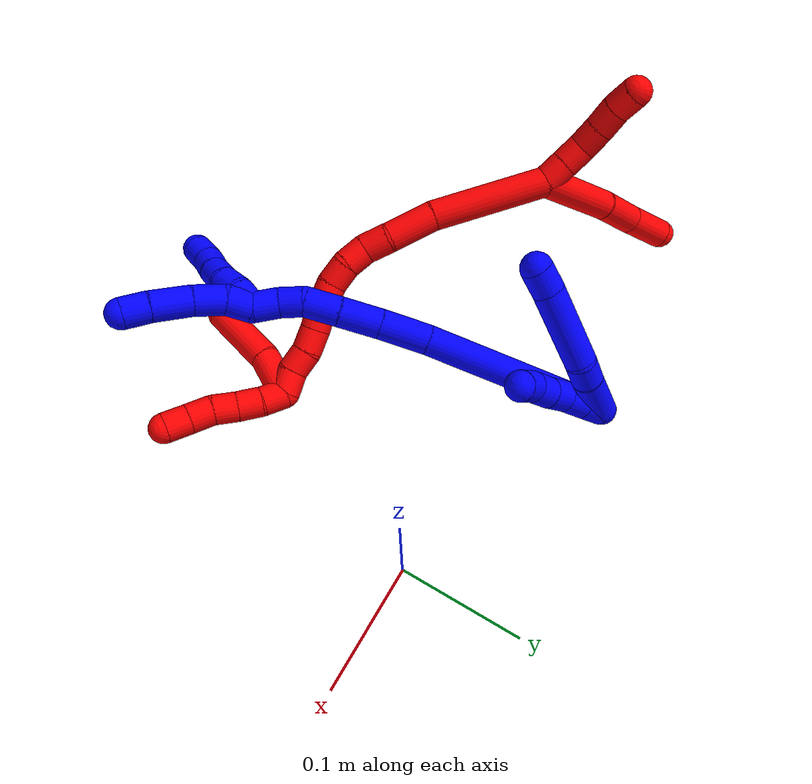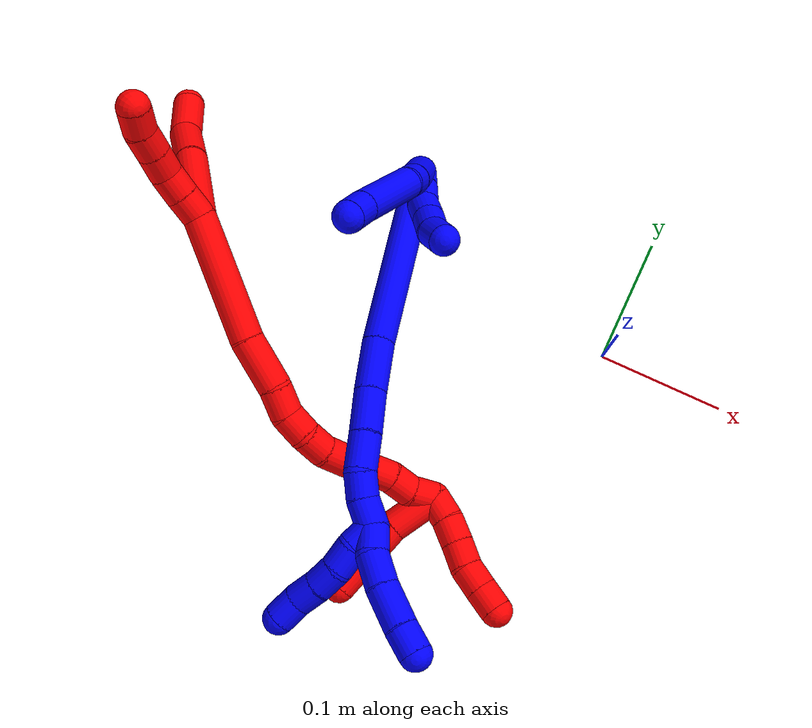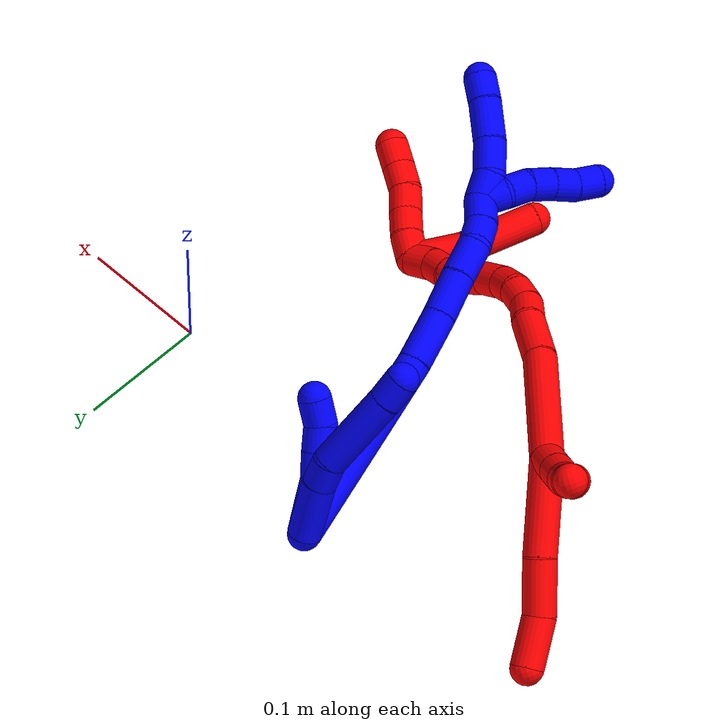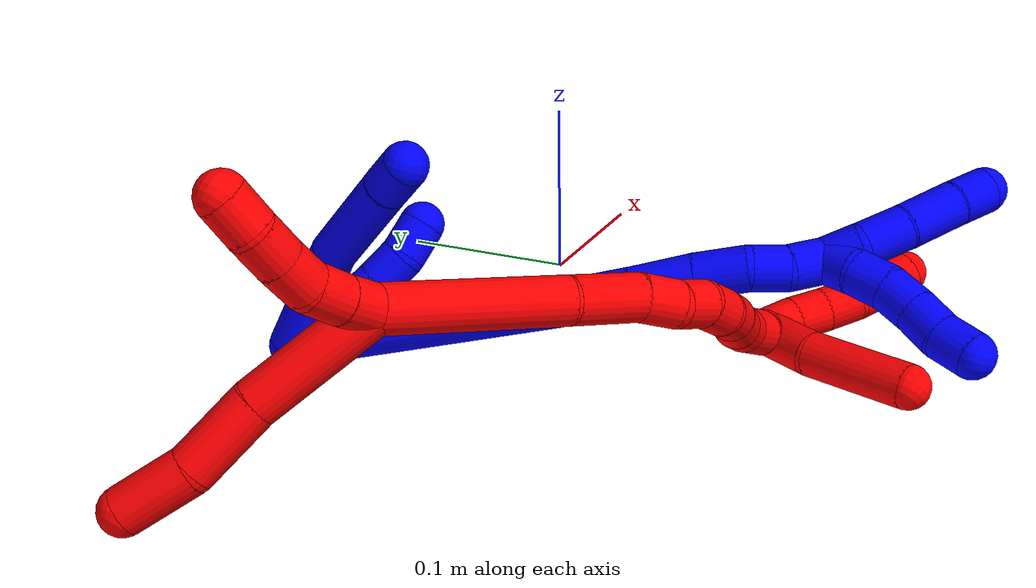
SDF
<sdf version="1.7">
 <world name="default">
  <plugin name="TubeGeneratorPlugin" filename="libtube_generator_plugin.so"/>
  <model name="photoneo_s_sensor">
   <static>1</static>
   <pose>0 0 2 1.57079 1.57079 3.14159</pose>
   <link name="link">
    <inertial><mass>0.1</mass></inertial>
    <sensor name="sensor" type="depth">
     <update_rate>30</update_rate>
     <camera>
      <horizontal_fov>1.22</horizontal_fov>
      <image><width>1920</width><height>1200</height><format>B8G8R8</format></image>
      <clip><near>0.1</near><far>4</far></clip>
      <depth_camera><output>points</output></depth_camera>
     </camera>
     <plugin name="camera_plugin" filename="libgazebo_ros_depth_camera.so">
      <baseline>0.2</baseline>
      <alwaysOn>1</alwaysOn>
      <updateRate>0.0</updateRate>
      <cameraName>camera_ir</cameraName>
      <imageTopicName>/camera/color/image_raw</imageTopicName>
      <cameraInfoTopicName>/camera/color/camera_info</cameraInfoTopicName>
      <depthImageTopicName>/camera/depth/image_raw</depthImageTopicName>
      <depthImageCameraInfoTopicName>/camera/depth/camera_info</depthImageCameraInfoTopicName>
      <pointCloudTopicName>/camera/depth/points</pointCloudTopicName>
      <frameName>fr_optical</frameName>
      <pointCloudCutoff>0.1</pointCloudCutoff>
      <pointCloudCutoffMax>2.0</pointCloudCutoffMax>
      <distortionK1>0</distortionK1>
      <distortionK2>0</distortionK2>
      <distortionK3>0</distortionK3>
      <distortionT1>0</distortionT1>
      <distortionT2>0</distortionT2>
      <CxPrime>0</CxPrime>
      <Cx>0</Cx>
      <Cy>0</Cy>
      <focalLength>0</focalLength>
      <hackBaseline>0</hackBaseline>
     </plugin>
    </sensor>
   </link>
  </model>
  <gravity>0 0 -9.8</gravity>
  <magnetic_field>6e-06 2.3e-05 -4.2e-05</magnetic_field>
  <atmosphere type="adiabatic"/>
  <physics name="default_physics" default="0" type="ode">
   <max_step_size>0.003</max_step_size>
   <real_time_factor>1</real_time_factor>
   <real_time_update_rate>1000</real_time_update_rate>
   <max_contacts>10000</max_contacts>
   <ode>
    <solver>
     <type>quick</type>
     <iters>100</iters>
     <sor>1.3</sor>
     <use_dynamic_moi_rescaling>0</use_dynamic_moi_rescaling>
    </solver>
    <constraints>
     <contact_max_correcting_vel>0</contact_max_correcting_vel>
     <contact_surface_layer>0.001</contact_surface_layer>
     <cfm>0</cfm>
     <erp>0.2</erp>
    </constraints>
   </ode>
  </physics>
  <scene><ambient>0.4 0.4 0.4 1</ambient><background>0.7 0.7 0.7 1</background><shadows>0</shadows></scene>
  <audio><device>default</device></audio>
  <spherical_coordinates>
   <surface_model>EARTH_WGS84</surface_model>
   <latitude_deg>0</latitude_deg>
   <longitude_deg>0</longitude_deg>
   <elevation>0</elevation>
   <heading_deg>0</heading_deg>
  </spherical_coordinates>
  <model name="bin">
   <static>1</static>
   <link name="bottom">
    <collision name="collision-bottom">
     <pose>0 0 -0.01 0 -0 0</pose>
     <geometry><box><size>0.8 0.6 0.02</size></box></geometry>
     <surface>
      <friction><ode><mu>100</mu><mu2>100</mu2></ode></friction>
      <contact><collide_bitmask>65535</collide_bitmask></contact>
     </surface>
    </collision>
   </link>
   <link name="west_wall">
    <collision name="collision-west_wall">
     <pose>-0.41 0 0.1 0 -0 0</pose>
     <geometry><box><size>0.02 0.6 0.2</size></box></geometry>
     <surface>
      <friction><ode><mu>100</mu><mu2>100</mu2></ode></friction>
      <contact><collide_bitmask>65535</collide_bitmask></contact>
     </surface>
    </collision>
   </link>
   <link name="east_wall">
    <collision name="collision-east_wall">
     <pose>0.41 0 0.1 0 -0 0</pose>
     <geometry><box><size>0.02 0.6 0.2</size></box></geometry>
     <surface>
      <friction><ode><mu>100</mu><mu2>100</mu2></ode></friction>
      <contact><collide_bitmask>65535</collide_bitmask></contact>
     </surface>
    </collision>
   </link>
   <link name="south_wall">
    <collision name="collision-south_wall">
     <pose>0 -0.31 0.1 0 -0 0</pose>
     <geometry><box><size>0.8 0.02 0.2</size></box></geometry>
     <surface>
      <friction><ode><mu>100</mu><mu2>100</mu2></ode></friction>
      <contact><collide_bitmask>65535</collide_bitmask></contact>
     </surface>
    </collision>
   </link>
   <link name="north_wall">
    <collision name="collision-north_wall">
     <pose>0 0.31 0.1 0 -0 0</pose>
     <geometry><box><size>0.8 0.02 0.2</size></box></geometry>
     <surface>
      <friction><ode><mu>100</mu><mu2>100</mu2></ode></friction>
      <contact><collide_bitmask>65535</collide_bitmask></contact>
     </surface>
    </collision>
   </link>
  </model>
  <model name="1">
   <static>0</static>
   <link name="1">
    <collision name="collision-cylinder-e_1_2_8">
     <pose>0.005212 0.000737 -0.021674 -3.1076 0.235873 -2.85663</pose>
     <geometry><cylinder><radius>0.0125</radius><length>0.044609</length></cylinder></geometry>
     <surface>
      <friction><ode><mu>1.16</mu><mu2>1.16</mu2><slip1>0</slip1><slip2>0</slip2></ode></friction>
      <contact><ode><kp>1e+06</kp><kd>1</kd><max_vel>0</max_vel><min_depth>0.001</min_depth></ode></contact>
     </surface>
    </collision>
    <visual name="visual-cylinder-e_1_2_8">
     <pose>0.005212 0.000737 -0.021674 -3.1076 0.235873 -2.85663</pose>
     <geometry><cylinder><radius>0.0125</radius><length>0.044609</length></cylinder></geometry>
     <material><ambient>0 0 1 1</ambient></material>
    </visual>
    <collision name="collision-cylinder-e_2_8_9">
     <pose>0.013745 0.002618 -0.052989 -3.0235 0.329599 -2.45853</pose>
     <geometry><cylinder><radius>0.0125</radius><length>0.02052</length></cylinder></geometry>
     <surface>
      <friction><ode><mu>1.16</mu><mu2>1.16</mu2><slip1>0</slip1><slip2>0</slip2></ode></friction>
      <contact><ode><kp>1e+06</kp><kd>1</kd><max_vel>0</max_vel><min_depth>0.001</min_depth></ode></contact>
     </surface>
    </collision>
    <visual name="visual-cylinder-e_2_8_9">
     <pose>0.013745 0.002618 -0.052989 -3.0235 0.329599 -2.45853</pose>
     <geometry><cylinder><radius>0.0125</radius><length>0.02052</length></cylinder></geometry>
     <material><ambient>0 0 1 1</ambient></material>
    </visual>
    <collision name="collision-cylinder-e_3_9_10">
     <pose>0.035737 0.009478 -0.088163 -2.92136 0.619756 -2.47662</pose>
     <geometry><cylinder><radius>0.0125</radius><length>0.064289</length></cylinder></geometry>
     <surface>
      <friction><ode><mu>1.16</mu><mu2>1.16</mu2><slip1>0</slip1><slip2>0</slip2></ode></friction>
      <contact><ode><kp>1e+06</kp><kd>1</kd><max_vel>0</max_vel><min_depth>0.001</min_depth></ode></contact>
     </surface>
    </collision>
    <visual name="visual-cylinder-e_3_9_10">
     <pose>0.035737 0.009478 -0.088163 -2.92136 0.619756 -2.47662</pose>
     <geometry><cylinder><radius>0.0125</radius><length>0.064289</length></cylinder></geometry>
     <material><ambient>0 0 1 1</ambient></material>
    </visual>
    <collision name="collision-cylinder-e_4_10_6">
     <pose>0.0602 0.016362 -0.122123 -3.00387 0.597786 -2.70117</pose>
     <geometry><cylinder><radius>0.0125</radius><length>0.020582</length></cylinder></geometry>
     <surface>
      <friction><ode><mu>1.16</mu><mu2>1.16</mu2><slip1>0</slip1><slip2>0</slip2></ode></friction>
      <contact><ode><kp>1e+06</kp><kd>1</kd><max_vel>0</max_vel><min_depth>0.001</min_depth></ode></contact>
     </surface>
    </collision>
    <visual name="visual-cylinder-e_4_10_6">
     <pose>0.0602 0.016362 -0.122123 -3.00387 0.597786 -2.70117</pose>
     <geometry><cylinder><radius>0.0125</radius><length>0.020582</length></cylinder></geometry>
     <material><ambient>0 0 1 1</ambient></material>
    </visual>
    <collision name="collision-cylinder-e_1_2_11">
     <pose>0.004333 -0.004591 -0.007755 2.6071 0.448185 1.38843</pose>
     <geometry><cylinder><radius>0.0125</radius><length>0.02</length></cylinder></geometry>
     <surface>
      <friction><ode><mu>1.16</mu><mu2>1.16</mu2><slip1>0</slip1><slip2>0</slip2></ode></friction>
      <contact><ode><kp>1e+06</kp><kd>1</kd><max_vel>0</max_vel><min_depth>0.001</min_depth></ode></contact>
     </surface>
    </collision>
    <visual name="visual-cylinder-e_1_2_11">
     <pose>0.004333 -0.004591 -0.007755 2.6071 0.448185 1.38843</pose>
     <geometry><cylinder><radius>0.0125</radius><length>0.02</length></cylinder></geometry>
     <material><ambient>0 0 1 1</ambient></material>
    </visual>
    <collision name="collision-cylinder-e_2_11_12">
     <pose>0.013136 -0.013777 -0.023186 2.60211 0.463328 1.41272</pose>
     <geometry><cylinder><radius>0.0125</radius><length>0.02</length></cylinder></geometry>
     <surface>
      <friction><ode><mu>1.16</mu><mu2>1.16</mu2><slip1>0</slip1><slip2>0</slip2></ode></friction>
      <contact><ode><kp>1e+06</kp><kd>1</kd><max_vel>0</max_vel><min_depth>0.001</min_depth></ode></contact>
     </surface>
    </collision>
    <visual name="visual-cylinder-e_2_11_12">
     <pose>0.013136 -0.013777 -0.023186 2.60211 0.463328 1.41272</pose>
     <geometry><cylinder><radius>0.0125</radius><length>0.02</length></cylinder></geometry>
     <material><ambient>0 0 1 1</ambient></material>
    </visual>
    <collision name="collision-cylinder-e_3_12_13">
     <pose>0.01994 -0.023313 -0.039236 2.60868 0.235678 0.818495</pose>
     <geometry><cylinder><radius>0.0125</radius><length>0.02</length></cylinder></geometry>
     <surface>
      <friction><ode><mu>1.16</mu><mu2>1.16</mu2><slip1>0</slip1><slip2>0</slip2></ode></friction>
      <contact><ode><kp>1e+06</kp><kd>1</kd><max_vel>0</max_vel><min_depth>0.001</min_depth></ode></contact>
     </surface>
    </collision>
    <visual name="visual-cylinder-e_3_12_13">
     <pose>0.01994 -0.023313 -0.039236 2.60868 0.235678 0.818495</pose>
     <geometry><cylinder><radius>0.0125</radius><length>0.02</length></cylinder></geometry>
     <material><ambient>0 0 1 1</ambient></material>
    </visual>
    <collision name="collision-cylinder-e_4_13_14">
     <pose>0.024799 -0.032339 -0.056383 2.7056 0.255095 1.04957</pose>
     <geometry><cylinder><radius>0.0125</radius><length>0.02</length></cylinder></geometry>
     <surface>
      <friction><ode><mu>1.16</mu><mu2>1.16</mu2><slip1>0</slip1><slip2>0</slip2></ode></friction>
      <contact><ode><kp>1e+06</kp><kd>1</kd><max_vel>0</max_vel><min_depth>0.001</min_depth></ode></contact>
     </surface>
    </collision>
    <visual name="visual-cylinder-e_4_13_14">
     <pose>0.024799 -0.032339 -0.056383 2.7056 0.255095 1.04957</pose>
     <geometry><cylinder><radius>0.0125</radius><length>0.02</length></cylinder></geometry>
     <material><ambient>0 0 1 1</ambient></material>
    </visual>
    <collision name="collision-cylinder-e_5_14_5">
     <pose>0.026613 -0.040813 -0.074112 2.68615 -0.070971 -0.304018</pose>
     <geometry><cylinder><radius>0.0125</radius><length>0.02</length></cylinder></geometry>
     <surface>
      <friction><ode><mu>1.16</mu><mu2>1.16</mu2><slip1>0</slip1><slip2>0</slip2></ode></friction>
      <contact><ode><kp>1e+06</kp><kd>1</kd><max_vel>0</max_vel><min_depth>0.001</min_depth></ode></contact>
     </surface>
    </collision>
    <visual name="visual-cylinder-e_5_14_5">
     <pose>0.026613 -0.040813 -0.074112 2.68615 -0.070971 -0.304018</pose>
     <geometry><cylinder><radius>0.0125</radius><length>0.02</length></cylinder></geometry>
     <material><ambient>0 0 1 1</ambient></material>
    </visual>
    <collision name="collision-cylinder-e_1_2_15">
     <pose>0.057586 -0.035045 -0.036986 2.38315 0.846446 1.69299</pose>
     <geometry><cylinder><radius>0.0125</radius><length>0.153783</length></cylinder></geometry>
     <surface>
      <friction><ode><mu>1.16</mu><mu2>1.16</mu2><slip1>0</slip1><slip2>0</slip2></ode></friction>
      <contact><ode><kp>1e+06</kp><kd>1</kd><max_vel>0</max_vel><min_depth>0.001</min_depth></ode></contact>
     </surface>
    </collision>
    <visual name="visual-cylinder-e_1_2_15">
     <pose>0.057586 -0.035045 -0.036986 2.38315 0.846446 1.69299</pose>
     <geometry><cylinder><radius>0.0125</radius><length>0.153783</length></cylinder></geometry>
     <material><ambient>0 0 1 1</ambient></material>
    </visual>
    <collision name="collision-cylinder-e_2_15_16">
     <pose>0.129521 -0.080545 -0.084227 2.34649 0.775161 1.54259</pose>
     <geometry><cylinder><radius>0.0125</radius><length>0.041005</length></cylinder></geometry>
     <surface>
      <friction><ode><mu>1.16</mu><mu2>1.16</mu2><slip1>0</slip1><slip2>0</slip2></ode></friction>
      <contact><ode><kp>1e+06</kp><kd>1</kd><max_vel>0</max_vel><min_depth>0.001</min_depth></ode></contact>
     </surface>
    </collision>
    <visual name="visual-cylinder-e_2_15_16">
     <pose>0.129521 -0.080545 -0.084227 2.34649 0.775161 1.54259</pose>
     <geometry><cylinder><radius>0.0125</radius><length>0.041005</length></cylinder></geometry>
     <material><ambient>0 0 1 1</ambient></material>
    </visual>
    <collision name="collision-cylinder-e_3_16_17">
     <pose>0.155215 -0.100175 -0.103266 2.33449 0.729086 1.45866</pose>
     <geometry><cylinder><radius>0.0125</radius><length>0.034063</length></cylinder></geometry>
     <surface>
      <friction><ode><mu>1.16</mu><mu2>1.16</mu2><slip1>0</slip1><slip2>0</slip2></ode></friction>
      <contact><ode><kp>1e+06</kp><kd>1</kd><max_vel>0</max_vel><min_depth>0.001</min_depth></ode></contact>
     </surface>
    </collision>
    <visual name="visual-cylinder-e_3_16_17">
     <pose>0.155215 -0.100175 -0.103266 2.33449 0.729086 1.45866</pose>
     <geometry><cylinder><radius>0.0125</radius><length>0.034063</length></cylinder></geometry>
     <material><ambient>0 0 1 1</ambient></material>
    </visual>
    <collision name="collision-cylinder-e_4_17_18">
     <pose>0.176625 -0.117102 -0.118588 2.27128 0.781593 1.45031</pose>
     <geometry><cylinder><radius>0.0125</radius><length>0.028574</length></cylinder></geometry>
     <surface>
      <friction><ode><mu>1.16</mu><mu2>1.16</mu2><slip1>0</slip1><slip2>0</slip2></ode></friction>
      <contact><ode><kp>1e+06</kp><kd>1</kd><max_vel>0</max_vel><min_depth>0.001</min_depth></ode></contact>
     </surface>
    </collision>
    <visual name="visual-cylinder-e_4_17_18">
     <pose>0.176625 -0.117102 -0.118588 2.27128 0.781593 1.45031</pose>
     <geometry><cylinder><radius>0.0125</radius><length>0.028574</length></cylinder></geometry>
     <material><ambient>0 0 1 1</ambient></material>
    </visual>
    <collision name="collision-cylinder-e_5_18_19">
     <pose>0.192687 -0.132679 -0.12762 1.87955 0.630801 0.83998</pose>
     <geometry><cylinder><radius>0.0125</radius><length>0.020338</length></cylinder></geometry>
     <surface>
      <friction><ode><mu>1.16</mu><mu2>1.16</mu2><slip1>0</slip1><slip2>0</slip2></ode></friction>
      <contact><ode><kp>1e+06</kp><kd>1</kd><max_vel>0</max_vel><min_depth>0.001</min_depth></ode></contact>
     </surface>
    </collision>
    <visual name="visual-cylinder-e_5_18_19">
     <pose>0.192687 -0.132679 -0.12762 1.87955 0.630801 0.83998</pose>
     <geometry><cylinder><radius>0.0125</radius><length>0.020338</length></cylinder></geometry>
     <material><ambient>0 0 1 1</ambient></material>
    </visual>
    <collision name="collision-cylinder-e_6_19_1">
     <pose>0.202695 -0.150089 -0.134069 1.96193 0.368986 0.543821</pose>
     <geometry><cylinder><radius>0.0125</radius><length>0.022237</length></cylinder></geometry>
     <surface>
      <friction><ode><mu>1.16</mu><mu2>1.16</mu2><slip1>0</slip1><slip2>0</slip2></ode></friction>
      <contact><ode><kp>1e+06</kp><kd>1</kd><max_vel>0</max_vel><min_depth>0.001</min_depth></ode></contact>
     </surface>
    </collision>
    <visual name="visual-cylinder-e_6_19_1">
     <pose>0.202695 -0.150089 -0.134069 1.96193 0.368986 0.543821</pose>
     <geometry><cylinder><radius>0.0125</radius><length>0.022237</length></cylinder></geometry>
     <material><ambient>0 0 1 1</ambient></material>
    </visual>
    <collision name="collision-cylinder-e_1_1_20">
     <pose>0.212538 -0.165193 -0.144807 2.45887 0.588301 1.41212</pose>
     <geometry><cylinder><radius>0.0125</radius><length>0.021023</length></cylinder></geometry>
     <surface>
      <friction><ode><mu>1.16</mu><mu2>1.16</mu2><slip1>0</slip1><slip2>0</slip2></ode></friction>
      <contact><ode><kp>1e+06</kp><kd>1</kd><max_vel>0</max_vel><min_depth>0.001</min_depth></ode></contact>
     </surface>
    </collision>
    <visual name="visual-cylinder-e_1_1_20">
     <pose>0.212538 -0.165193 -0.144807 2.45887 0.588301 1.41212</pose>
     <geometry><cylinder><radius>0.0125</radius><length>0.021023</length></cylinder></geometry>
     <material><ambient>0 0 1 1</ambient></material>
    </visual>
    <collision name="collision-cylinder-e_2_20_21">
     <pose>0.222722 -0.180468 -0.158717 2.20154 0.345593 0.661885</pose>
     <geometry><cylinder><radius>0.0125</radius><length>0.025684</length></cylinder></geometry>
     <surface>
      <friction><ode><mu>1.16</mu><mu2>1.16</mu2><slip1>0</slip1><slip2>0</slip2></ode></friction>
      <contact><ode><kp>1e+06</kp><kd>1</kd><max_vel>0</max_vel><min_depth>0.001</min_depth></ode></contact>
     </surface>
    </collision>
    <visual name="visual-cylinder-e_2_20_21">
     <pose>0.222722 -0.180468 -0.158717 2.20154 0.345593 0.661885</pose>
     <geometry><cylinder><radius>0.0125</radius><length>0.025684</length></cylinder></geometry>
     <material><ambient>0 0 1 1</ambient></material>
    </visual>
    <collision name="collision-cylinder-e_3_21_22">
     <pose>0.230812 -0.203466 -0.174325 2.14064 0.233539 0.422556</pose>
     <geometry><cylinder><radius>0.0125</radius><length>0.032326</length></cylinder></geometry>
     <surface>
      <friction><ode><mu>1.16</mu><mu2>1.16</mu2><slip1>0</slip1><slip2>0</slip2></ode></friction>
      <contact><ode><kp>1e+06</kp><kd>1</kd><max_vel>0</max_vel><min_depth>0.001</min_depth></ode></contact>
     </surface>
    </collision>
    <visual name="visual-cylinder-e_3_21_22">
     <pose>0.230812 -0.203466 -0.174325 2.14064 0.233539 0.422556</pose>
     <geometry><cylinder><radius>0.0125</radius><length>0.032326</length></cylinder></geometry>
     <material><ambient>0 0 1 1</ambient></material>
    </visual>
    <collision name="collision-cylinder-e_4_22_4">
     <pose>0.236466 -0.225818 -0.187626 2.05708 0.183481 0.303049</pose>
     <geometry><cylinder><radius>0.0125</radius><length>0.020967</length></cylinder></geometry>
     <surface>
      <friction><ode><mu>1.16</mu><mu2>1.16</mu2><slip1>0</slip1><slip2>0</slip2></ode></friction>
      <contact><ode><kp>1e+06</kp><kd>1</kd><max_vel>0</max_vel><min_depth>0.001</min_depth></ode></contact>
     </surface>
    </collision>
    <visual name="visual-cylinder-e_4_22_4">
     <pose>0.236466 -0.225818 -0.187626 2.05708 0.183481 0.303049</pose>
     <geometry><cylinder><radius>0.0125</radius><length>0.020967</length></cylinder></geometry>
     <material><ambient>0 0 1 1</ambient></material>
    </visual>
    <collision name="collision-cylinder-e_1_1_23">
     <pose>0.216648 -0.159526 -0.139074 -2.99963 1.46433 -2.98372</pose>
     <geometry><cylinder><radius>0.0125</radius><length>0.02</length></cylinder></geometry>
     <surface>
      <friction><ode><mu>1.16</mu><mu2>1.16</mu2><slip1>0</slip1><slip2>0</slip2></ode></friction>
      <contact><ode><kp>1e+06</kp><kd>1</kd><max_vel>0</max_vel><min_depth>0.001</min_depth></ode></contact>
     </surface>
    </collision>
    <visual name="visual-cylinder-e_1_1_23">
     <pose>0.216648 -0.159526 -0.139074 -2.99963 1.46433 -2.98372</pose>
     <geometry><cylinder><radius>0.0125</radius><length>0.02</length></cylinder></geometry>
     <material><ambient>0 0 1 1</ambient></material>
    </visual>
    <collision name="collision-cylinder-e_2_23_24">
     <pose>0.236384 -0.161372 -0.139769 1.39386 1.36662 1.19638</pose>
     <geometry><cylinder><radius>0.0125</radius><length>0.02</length></cylinder></geometry>
     <surface>
      <friction><ode><mu>1.16</mu><mu2>1.16</mu2><slip1>0</slip1><slip2>0</slip2></ode></friction>
      <contact><ode><kp>1e+06</kp><kd>1</kd><max_vel>0</max_vel><min_depth>0.001</min_depth></ode></contact>
     </surface>
    </collision>
    <visual name="visual-cylinder-e_2_23_24">
     <pose>0.236384 -0.161372 -0.139769 1.39386 1.36662 1.19638</pose>
     <geometry><cylinder><radius>0.0125</radius><length>0.02</length></cylinder></geometry>
     <material><ambient>0 0 1 1</ambient></material>
    </visual>
    <collision name="collision-cylinder-e_3_24_25">
     <pose>0.255907 -0.163929 -0.137175 0.245801 1.33807 0.194718</pose>
     <geometry><cylinder><radius>0.0125</radius><length>0.02</length></cylinder></geometry>
     <surface>
      <friction><ode><mu>1.16</mu><mu2>1.16</mu2><slip1>0</slip1><slip2>0</slip2></ode></friction>
      <contact><ode><kp>1e+06</kp><kd>1</kd><max_vel>0</max_vel><min_depth>0.001</min_depth></ode></contact>
     </surface>
    </collision>
    <visual name="visual-cylinder-e_3_24_25">
     <pose>0.255907 -0.163929 -0.137175 0.245801 1.33807 0.194718</pose>
     <geometry><cylinder><radius>0.0125</radius><length>0.02</length></cylinder></geometry>
     <material><ambient>0 0 1 1</ambient></material>
    </visual>
    <collision name="collision-cylinder-e_4_25_26">
     <pose>0.275271 -0.163933 -0.132318 -0.209442 1.29958 -0.159396</pose>
     <geometry><cylinder><radius>0.0125</radius><length>0.02</length></cylinder></geometry>
     <surface>
      <friction><ode><mu>1.16</mu><mu2>1.16</mu2><slip1>0</slip1><slip2>0</slip2></ode></friction>
      <contact><ode><kp>1e+06</kp><kd>1</kd><max_vel>0</max_vel><min_depth>0.001</min_depth></ode></contact>
     </surface>
    </collision>
    <visual name="visual-cylinder-e_4_25_26">
     <pose>0.275271 -0.163933 -0.132318 -0.209442 1.29958 -0.159396</pose>
     <geometry><cylinder><radius>0.0125</radius><length>0.02</length></cylinder></geometry>
     <material><ambient>0 0 1 1</ambient></material>
    </visual>
    <collision name="collision-cylinder-e_5_26_3">
     <pose>0.294864 -0.163828 -0.128899 0.51508 1.47898 0.471566</pose>
     <geometry><cylinder><radius>0.0125</radius><length>0.02</length></cylinder></geometry>
     <surface>
      <friction><ode><mu>1.16</mu><mu2>1.16</mu2><slip1>0</slip1><slip2>0</slip2></ode></friction>
      <contact><ode><kp>1e+06</kp><kd>1</kd><max_vel>0</max_vel><min_depth>0.001</min_depth></ode></contact>
     </surface>
    </collision>
    <visual name="visual-cylinder-e_5_26_3">
     <pose>0.294864 -0.163828 -0.128899 0.51508 1.47898 0.471566</pose>
     <geometry><cylinder><radius>0.0125</radius><length>0.02</length></cylinder></geometry>
     <material><ambient>0 0 1 1</ambient></material>
    </visual>
    <collision name="collision-sphere-3">
     <pose>0.304822 -0.164279 -0.128102 0 -0 0</pose>
     <geometry><sphere><radius>0.0125</radius></sphere></geometry>
     <surface>
      <friction><ode><mu>1.16</mu><mu2>1.16</mu2><slip1>0</slip1><slip2>0</slip2></ode></friction>
      <contact><ode><kp>1e+06</kp><kd>1</kd><max_vel>0</max_vel><min_depth>0.001</min_depth></ode></contact>
     </surface>
    </collision>
    <visual name="visual-sphere-3">
     <pose>0.304822 -0.164279 -0.128102 0 -0 0</pose>
     <geometry><sphere><radius>0.0125</radius></sphere></geometry>
     <material><ambient>0 0 1 1</ambient></material>
    </visual>
    <collision name="collision-sphere-26">
     <pose>0.284906 -0.163376 -0.129697 0 -0 0</pose>
     <geometry><sphere><radius>0.0125</radius></sphere></geometry>
     <surface>
      <friction><ode><mu>1.16</mu><mu2>1.16</mu2><slip1>0</slip1><slip2>0</slip2></ode></friction>
      <contact><ode><kp>1e+06</kp><kd>1</kd><max_vel>0</max_vel><min_depth>0.001</min_depth></ode></contact>
     </surface>
    </collision>
    <visual name="visual-sphere-26">
     <pose>0.284906 -0.163376 -0.129697 0 -0 0</pose>
     <geometry><sphere><radius>0.0125</radius></sphere></geometry>
     <material><ambient>0 0 1 1</ambient></material>
    </visual>
    <collision name="collision-sphere-25">
     <pose>0.265637 -0.16449 -0.134938 0 -0 0</pose>
     <geometry><sphere><radius>0.0125</radius></sphere></geometry>
     <surface>
      <friction><ode><mu>1.16</mu><mu2>1.16</mu2><slip1>0</slip1><slip2>0</slip2></ode></friction>
      <contact><ode><kp>1e+06</kp><kd>1</kd><max_vel>0</max_vel><min_depth>0.001</min_depth></ode></contact>
     </surface>
    </collision>
    <visual name="visual-sphere-25">
     <pose>0.265637 -0.16449 -0.134938 0 -0 0</pose>
     <geometry><sphere><radius>0.0125</radius></sphere></geometry>
     <material><ambient>0 0 1 1</ambient></material>
    </visual>
    <collision name="collision-sphere-24">
     <pose>0.246176 -0.163368 -0.139412 0 -0 0</pose>
     <geometry><sphere><radius>0.0125</radius></sphere></geometry>
     <surface>
      <friction><ode><mu>1.16</mu><mu2>1.16</mu2><slip1>0</slip1><slip2>0</slip2></ode></friction>
      <contact><ode><kp>1e+06</kp><kd>1</kd><max_vel>0</max_vel><min_depth>0.001</min_depth></ode></contact>
     </surface>
    </collision>
    <visual name="visual-sphere-24">
     <pose>0.246176 -0.163368 -0.139412 0 -0 0</pose>
     <geometry><sphere><radius>0.0125</radius></sphere></geometry>
     <material><ambient>0 0 1 1</ambient></material>
    </visual>
    <collision name="collision-sphere-23">
     <pose>0.226592 -0.159376 -0.140126 0 -0 0</pose>
     <geometry><sphere><radius>0.0125</radius></sphere></geometry>
     <surface>
      <friction><ode><mu>1.16</mu><mu2>1.16</mu2><slip1>0</slip1><slip2>0</slip2></ode></friction>
      <contact><ode><kp>1e+06</kp><kd>1</kd><max_vel>0</max_vel><min_depth>0.001</min_depth></ode></contact>
     </surface>
    </collision>
    <visual name="visual-sphere-23">
     <pose>0.226592 -0.159376 -0.140126 0 -0 0</pose>
     <geometry><sphere><radius>0.0125</radius></sphere></geometry>
     <material><ambient>0 0 1 1</ambient></material>
    </visual>
    <collision name="collision-sphere-4">
     <pose>0.238378 -0.23493 -0.192443 0 -0 0</pose>
     <geometry><sphere><radius>0.0125</radius></sphere></geometry>
     <surface>
      <friction><ode><mu>1.16</mu><mu2>1.16</mu2><slip1>0</slip1><slip2>0</slip2></ode></friction>
      <contact><ode><kp>1e+06</kp><kd>1</kd><max_vel>0</max_vel><min_depth>0.001</min_depth></ode></contact>
     </surface>
    </collision>
    <visual name="visual-sphere-4">
     <pose>0.238378 -0.23493 -0.192443 0 -0 0</pose>
     <geometry><sphere><radius>0.0125</radius></sphere></geometry>
     <material><ambient>0 0 1 1</ambient></material>
    </visual>
    <collision name="collision-sphere-22">
     <pose>0.234553 -0.216705 -0.182809 0 -0 0</pose>
     <geometry><sphere><radius>0.0125</radius></sphere></geometry>
     <surface>
      <friction><ode><mu>1.16</mu><mu2>1.16</mu2><slip1>0</slip1><slip2>0</slip2></ode></friction>
      <contact><ode><kp>1e+06</kp><kd>1</kd><max_vel>0</max_vel><min_depth>0.001</min_depth></ode></contact>
     </surface>
    </collision>
    <visual name="visual-sphere-22">
     <pose>0.234553 -0.216705 -0.182809 0 -0 0</pose>
     <geometry><sphere><radius>0.0125</radius></sphere></geometry>
     <material><ambient>0 0 1 1</ambient></material>
    </visual>
    <collision name="collision-sphere-21">
     <pose>0.227072 -0.190226 -0.165842 0 -0 0</pose>
     <geometry><sphere><radius>0.0125</radius></sphere></geometry>
     <surface>
      <friction><ode><mu>1.16</mu><mu2>1.16</mu2><slip1>0</slip1><slip2>0</slip2></ode></friction>
      <contact><ode><kp>1e+06</kp><kd>1</kd><max_vel>0</max_vel><min_depth>0.001</min_depth></ode></contact>
     </surface>
    </collision>
    <visual name="visual-sphere-21">
     <pose>0.227072 -0.190226 -0.165842 0 -0 0</pose>
     <geometry><sphere><radius>0.0125</radius></sphere></geometry>
     <material><ambient>0 0 1 1</ambient></material>
    </visual>
    <collision name="collision-sphere-20">
     <pose>0.218371 -0.17071 -0.151591 0 -0 0</pose>
     <geometry><sphere><radius>0.0125</radius></sphere></geometry>
     <surface>
      <friction><ode><mu>1.16</mu><mu2>1.16</mu2><slip1>0</slip1><slip2>0</slip2></ode></friction>
      <contact><ode><kp>1e+06</kp><kd>1</kd><max_vel>0</max_vel><min_depth>0.001</min_depth></ode></contact>
     </surface>
    </collision>
    <visual name="visual-sphere-20">
     <pose>0.218371 -0.17071 -0.151591 0 -0 0</pose>
     <geometry><sphere><radius>0.0125</radius></sphere></geometry>
     <material><ambient>0 0 1 1</ambient></material>
    </visual>
    <collision name="collision-sphere-11">
     <pose>0.008667 -0.009182 -0.015511 0 -0 0</pose>
     <geometry><sphere><radius>0.0125</radius></sphere></geometry>
     <surface>
      <friction><ode><mu>1.16</mu><mu2>1.16</mu2><slip1>0</slip1><slip2>0</slip2></ode></friction>
      <contact><ode><kp>1e+06</kp><kd>1</kd><max_vel>0</max_vel><min_depth>0.001</min_depth></ode></contact>
     </surface>
    </collision>
    <visual name="visual-sphere-11">
     <pose>0.008667 -0.009182 -0.015511 0 -0 0</pose>
     <geometry><sphere><radius>0.0125</radius></sphere></geometry>
     <material><ambient>0 0 1 1</ambient></material>
    </visual>
    <collision name="collision-sphere-6">
     <pose>0.065992 0.01753 -0.130549 0 -0 0</pose>
     <geometry><sphere><radius>0.0125</radius></sphere></geometry>
     <surface>
      <friction><ode><mu>1.16</mu><mu2>1.16</mu2><slip1>0</slip1><slip2>0</slip2></ode></friction>
      <contact><ode><kp>1e+06</kp><kd>1</kd><max_vel>0</max_vel><min_depth>0.001</min_depth></ode></contact>
     </surface>
    </collision>
    <visual name="visual-sphere-6">
     <pose>0.065992 0.01753 -0.130549 0 -0 0</pose>
     <geometry><sphere><radius>0.0125</radius></sphere></geometry>
     <material><ambient>0 0 1 1</ambient></material>
    </visual>
    <collision name="collision-sphere-10">
     <pose>0.054408 0.015194 -0.113697 0 -0 0</pose>
     <geometry><sphere><radius>0.0125</radius></sphere></geometry>
     <surface>
      <friction><ode><mu>1.16</mu><mu2>1.16</mu2><slip1>0</slip1><slip2>0</slip2></ode></friction>
      <contact><ode><kp>1e+06</kp><kd>1</kd><max_vel>0</max_vel><min_depth>0.001</min_depth></ode></contact>
     </surface>
    </collision>
    <visual name="visual-sphere-10">
     <pose>0.054408 0.015194 -0.113697 0 -0 0</pose>
     <geometry><sphere><radius>0.0125</radius></sphere></geometry>
     <material><ambient>0 0 1 1</ambient></material>
    </visual>
    <collision name="collision-sphere-9">
     <pose>0.017066 0.003762 -0.062629 0 -0 0</pose>
     <geometry><sphere><radius>0.0125</radius></sphere></geometry>
     <surface>
      <friction><ode><mu>1.16</mu><mu2>1.16</mu2><slip1>0</slip1><slip2>0</slip2></ode></friction>
      <contact><ode><kp>1e+06</kp><kd>1</kd><max_vel>0</max_vel><min_depth>0.001</min_depth></ode></contact>
     </surface>
    </collision>
    <visual name="visual-sphere-9">
     <pose>0.017066 0.003762 -0.062629 0 -0 0</pose>
     <geometry><sphere><radius>0.0125</radius></sphere></geometry>
     <material><ambient>0 0 1 1</ambient></material>
    </visual>
    <collision name="collision-sphere-2">
     <geometry><sphere><radius>0.0125</radius></sphere></geometry>
     <surface>
      <friction><ode><mu>1.16</mu><mu2>1.16</mu2><slip1>0</slip1><slip2>0</slip2></ode></friction>
      <contact><ode><kp>1e+06</kp><kd>1</kd><max_vel>0</max_vel><min_depth>0.001</min_depth></ode></contact>
     </surface>
    </collision>
    <visual name="visual-sphere-2">
     <geometry><sphere><radius>0.0125</radius></sphere></geometry>
     <material><ambient>0 0 1 1</ambient></material>
    </visual>
    <collision name="collision-sphere-19">
     <pose>0.198685 -0.140502 -0.130115 0 -0 0</pose>
     <geometry><sphere><radius>0.0125</radius></sphere></geometry>
     <surface>
      <friction><ode><mu>1.16</mu><mu2>1.16</mu2><slip1>0</slip1><slip2>0</slip2></ode></friction>
      <contact><ode><kp>1e+06</kp><kd>1</kd><max_vel>0</max_vel><min_depth>0.001</min_depth></ode></contact>
     </surface>
    </collision>
    <visual name="visual-sphere-19">
     <pose>0.198685 -0.140502 -0.130115 0 -0 0</pose>
     <geometry><sphere><radius>0.0125</radius></sphere></geometry>
     <material><ambient>0 0 1 1</ambient></material>
    </visual>
    <collision name="collision-sphere-8">
     <pose>0.010425 0.001474 -0.043349 0 -0 0</pose>
     <geometry><sphere><radius>0.0125</radius></sphere></geometry>
     <surface>
      <friction><ode><mu>1.16</mu><mu2>1.16</mu2><slip1>0</slip1><slip2>0</slip2></ode></friction>
      <contact><ode><kp>1e+06</kp><kd>1</kd><max_vel>0</max_vel><min_depth>0.001</min_depth></ode></contact>
     </surface>
    </collision>
    <visual name="visual-sphere-8">
     <pose>0.010425 0.001474 -0.043349 0 -0 0</pose>
     <geometry><sphere><radius>0.0125</radius></sphere></geometry>
     <material><ambient>0 0 1 1</ambient></material>
    </visual>
    <collision name="collision-sphere-12">
     <pose>0.017605 -0.018373 -0.030861 0 -0 0</pose>
     <geometry><sphere><radius>0.0125</radius></sphere></geometry>
     <surface>
      <friction><ode><mu>1.16</mu><mu2>1.16</mu2><slip1>0</slip1><slip2>0</slip2></ode></friction>
      <contact><ode><kp>1e+06</kp><kd>1</kd><max_vel>0</max_vel><min_depth>0.001</min_depth></ode></contact>
     </surface>
    </collision>
    <visual name="visual-sphere-12">
     <pose>0.017605 -0.018373 -0.030861 0 -0 0</pose>
     <geometry><sphere><radius>0.0125</radius></sphere></geometry>
     <material><ambient>0 0 1 1</ambient></material>
    </visual>
    <collision name="collision-sphere-13">
     <pose>0.022275 -0.028253 -0.047611 0 -0 0</pose>
     <geometry><sphere><radius>0.0125</radius></sphere></geometry>
     <surface>
      <friction><ode><mu>1.16</mu><mu2>1.16</mu2><slip1>0</slip1><slip2>0</slip2></ode></friction>
      <contact><ode><kp>1e+06</kp><kd>1</kd><max_vel>0</max_vel><min_depth>0.001</min_depth></ode></contact>
     </surface>
    </collision>
    <visual name="visual-sphere-13">
     <pose>0.022275 -0.028253 -0.047611 0 -0 0</pose>
     <geometry><sphere><radius>0.0125</radius></sphere></geometry>
     <material><ambient>0 0 1 1</ambient></material>
    </visual>
    <collision name="collision-sphere-14">
     <pose>0.027322 -0.036426 -0.065154 0 -0 0</pose>
     <geometry><sphere><radius>0.0125</radius></sphere></geometry>
     <surface>
      <friction><ode><mu>1.16</mu><mu2>1.16</mu2><slip1>0</slip1><slip2>0</slip2></ode></friction>
      <contact><ode><kp>1e+06</kp><kd>1</kd><max_vel>0</max_vel><min_depth>0.001</min_depth></ode></contact>
     </surface>
    </collision>
    <visual name="visual-sphere-14">
     <pose>0.027322 -0.036426 -0.065154 0 -0 0</pose>
     <geometry><sphere><radius>0.0125</radius></sphere></geometry>
     <material><ambient>0 0 1 1</ambient></material>
    </visual>
    <collision name="collision-sphere-5">
     <pose>0.025904 -0.045201 -0.08307 0 -0 0</pose>
     <geometry><sphere><radius>0.0125</radius></sphere></geometry>
     <surface>
      <friction><ode><mu>1.16</mu><mu2>1.16</mu2><slip1>0</slip1><slip2>0</slip2></ode></friction>
      <contact><ode><kp>1e+06</kp><kd>1</kd><max_vel>0</max_vel><min_depth>0.001</min_depth></ode></contact>
     </surface>
    </collision>
    <visual name="visual-sphere-5">
     <pose>0.025904 -0.045201 -0.08307 0 -0 0</pose>
     <geometry><sphere><radius>0.0125</radius></sphere></geometry>
     <material><ambient>0 0 1 1</ambient></material>
    </visual>
    <collision name="collision-sphere-15">
     <pose>0.115173 -0.070089 -0.073973 0 -0 0</pose>
     <geometry><sphere><radius>0.0125</radius></sphere></geometry>
     <surface>
      <friction><ode><mu>1.16</mu><mu2>1.16</mu2><slip1>0</slip1><slip2>0</slip2></ode></friction>
      <contact><ode><kp>1e+06</kp><kd>1</kd><max_vel>0</max_vel><min_depth>0.001</min_depth></ode></contact>
     </surface>
    </collision>
    <visual name="visual-sphere-15">
     <pose>0.115173 -0.070089 -0.073973 0 -0 0</pose>
     <geometry><sphere><radius>0.0125</radius></sphere></geometry>
     <material><ambient>0 0 1 1</ambient></material>
    </visual>
    <collision name="collision-sphere-16">
     <pose>0.143869 -0.091 -0.094482 0 -0 0</pose>
     <geometry><sphere><radius>0.0125</radius></sphere></geometry>
     <surface>
      <friction><ode><mu>1.16</mu><mu2>1.16</mu2><slip1>0</slip1><slip2>0</slip2></ode></friction>
      <contact><ode><kp>1e+06</kp><kd>1</kd><max_vel>0</max_vel><min_depth>0.001</min_depth></ode></contact>
     </surface>
    </collision>
    <visual name="visual-sphere-16">
     <pose>0.143869 -0.091 -0.094482 0 -0 0</pose>
     <geometry><sphere><radius>0.0125</radius></sphere></geometry>
     <material><ambient>0 0 1 1</ambient></material>
    </visual>
    <collision name="collision-sphere-17">
     <pose>0.166561 -0.109349 -0.112051 0 -0 0</pose>
     <geometry><sphere><radius>0.0125</radius></sphere></geometry>
     <surface>
      <friction><ode><mu>1.16</mu><mu2>1.16</mu2><slip1>0</slip1><slip2>0</slip2></ode></friction>
      <contact><ode><kp>1e+06</kp><kd>1</kd><max_vel>0</max_vel><min_depth>0.001</min_depth></ode></contact>
     </surface>
    </collision>
    <visual name="visual-sphere-17">
     <pose>0.166561 -0.109349 -0.112051 0 -0 0</pose>
     <geometry><sphere><radius>0.0125</radius></sphere></geometry>
     <material><ambient>0 0 1 1</ambient></material>
    </visual>
    <collision name="collision-sphere-18">
     <pose>0.186689 -0.124855 -0.125124 0 -0 0</pose>
     <geometry><sphere><radius>0.0125</radius></sphere></geometry>
     <surface>
      <friction><ode><mu>1.16</mu><mu2>1.16</mu2><slip1>0</slip1><slip2>0</slip2></ode></friction>
      <contact><ode><kp>1e+06</kp><kd>1</kd><max_vel>0</max_vel><min_depth>0.001</min_depth></ode></contact>
     </surface>
    </collision>
    <visual name="visual-sphere-18">
     <pose>0.186689 -0.124855 -0.125124 0 -0 0</pose>
     <geometry><sphere><radius>0.0125</radius></sphere></geometry>
     <material><ambient>0 0 1 1</ambient></material>
    </visual>
    <collision name="collision-sphere-1">
     <pose>0.206705 -0.159676 -0.138022 0 -0 0</pose>
     <geometry><sphere><radius>0.0125</radius></sphere></geometry>
     <surface>
      <friction><ode><mu>1.16</mu><mu2>1.16</mu2><slip1>0</slip1><slip2>0</slip2></ode></friction>
      <contact><ode><kp>1e+06</kp><kd>1</kd><max_vel>0</max_vel><min_depth>0.001</min_depth></ode></contact>
     </surface>
    </collision>
    <visual name="visual-sphere-1">
     <pose>0.206705 -0.159676 -0.138022 0 -0 0</pose>
     <geometry><sphere><radius>0.0125</radius></sphere></geometry>
     <material><ambient>0 0 1 1</ambient></material>
    </visual>
    <inertial>
     <pose>0.115925 -0.077896 -0.088144 0 -0 0</pose>
     <mass>0.75</mass>
     <inertia>
      <ixx>0.000205</ixx>
      <ixy>0</ixy>
      <ixz>0</ixz>
      <iyy>0.000415</iyy>
      <iyz>0</iyz>
      <izz>-0.000147</izz>
     </inertia>
    </inertial>
   </link>
   <pose>-0.194045 0.075015 0.011494 2.8632 0.13373 -1.97773</pose>
  </model>
  <model name="2">
   <static>0</static>
   <link name="2">
    <collision name="collision-cylinder-e_1_2_8">
     <pose>-0.014724 0.002936 0.031737 -0.092255 -0.432761 0.020293</pose>
     <geometry><cylinder><radius>0.0125</radius><length>0.070219</length></cylinder></geometry>
     <surface>
      <friction><ode><mu>1.16</mu><mu2>1.16</mu2><slip1>0</slip1><slip2>0</slip2></ode></friction>
      <contact><ode><kp>1e+06</kp><kd>1</kd><max_vel>0</max_vel><min_depth>0.001</min_depth></ode></contact>
     </surface>
    </collision>
    <visual name="visual-cylinder-e_1_2_8">
     <pose>-0.014724 0.002936 0.031737 -0.092255 -0.432761 0.020293</pose>
     <geometry><cylinder><radius>0.0125</radius><length>0.070219</length></cylinder></geometry>
     <material><ambient>1 0 0 1</ambient></material>
    </visual>
    <collision name="collision-cylinder-e_2_8_9">
     <pose>-0.036383 0.005463 0.083184 0.02078 -0.338271 -0.003549</pose>
     <geometry><cylinder><radius>0.0125</radius><length>0.041795</length></cylinder></geometry>
     <surface>
      <friction><ode><mu>1.16</mu><mu2>1.16</mu2><slip1>0</slip1><slip2>0</slip2></ode></friction>
      <contact><ode><kp>1e+06</kp><kd>1</kd><max_vel>0</max_vel><min_depth>0.001</min_depth></ode></contact>
     </surface>
    </collision>
    <visual name="visual-cylinder-e_2_8_9">
     <pose>-0.036383 0.005463 0.083184 0.02078 -0.338271 -0.003549</pose>
     <geometry><cylinder><radius>0.0125</radius><length>0.041795</length></cylinder></geometry>
     <material><ambient>1 0 0 1</ambient></material>
    </visual>
    <collision name="collision-cylinder-e_3_9_6">
     <pose>-0.054056 0.006446 0.118497 -0.089027 -0.600877 0.027598</pose>
     <geometry><cylinder><radius>0.0125</radius><length>0.037986</length></cylinder></geometry>
     <surface>
      <friction><ode><mu>1.16</mu><mu2>1.16</mu2><slip1>0</slip1><slip2>0</slip2></ode></friction>
      <contact><ode><kp>1e+06</kp><kd>1</kd><max_vel>0</max_vel><min_depth>0.001</min_depth></ode></contact>
     </surface>
    </collision>
    <visual name="visual-cylinder-e_3_9_6">
     <pose>-0.054056 0.006446 0.118497 -0.089027 -0.600877 0.027598</pose>
     <geometry><cylinder><radius>0.0125</radius><length>0.037986</length></cylinder></geometry>
     <material><ambient>1 0 0 1</ambient></material>
    </visual>
    <collision name="collision-cylinder-e_1_2_10">
     <pose>-0.000613 0.009511 0.003028 -1.26253 -0.061289 0.044812</pose>
     <geometry><cylinder><radius>0.0125</radius><length>0.02</length></cylinder></geometry>
     <surface>
      <friction><ode><mu>1.16</mu><mu2>1.16</mu2><slip1>0</slip1><slip2>0</slip2></ode></friction>
      <contact><ode><kp>1e+06</kp><kd>1</kd><max_vel>0</max_vel><min_depth>0.001</min_depth></ode></contact>
     </surface>
    </collision>
    <visual name="visual-cylinder-e_1_2_10">
     <pose>-0.000613 0.009511 0.003028 -1.26253 -0.061289 0.044812</pose>
     <geometry><cylinder><radius>0.0125</radius><length>0.02</length></cylinder></geometry>
     <material><ambient>1 0 0 1</ambient></material>
    </visual>
    <collision name="collision-cylinder-e_2_10_11">
     <pose>-0.002136 0.028697 0.008415 -1.33174 -0.09126 0.071708</pose>
     <geometry><cylinder><radius>0.0125</radius><length>0.02</length></cylinder></geometry>
     <surface>
      <friction><ode><mu>1.16</mu><mu2>1.16</mu2><slip1>0</slip1><slip2>0</slip2></ode></friction>
      <contact><ode><kp>1e+06</kp><kd>1</kd><max_vel>0</max_vel><min_depth>0.001</min_depth></ode></contact>
     </surface>
    </collision>
    <visual name="visual-cylinder-e_2_10_11">
     <pose>-0.002136 0.028697 0.008415 -1.33174 -0.09126 0.071708</pose>
     <geometry><cylinder><radius>0.0125</radius><length>0.02</length></cylinder></geometry>
     <material><ambient>1 0 0 1</ambient></material>
    </visual>
    <collision name="collision-cylinder-e_3_11_12">
     <pose>-0.004513 0.048233 0.009986 -1.65037 -0.147038 0.15918</pose>
     <geometry><cylinder><radius>0.0125</radius><length>0.02</length></cylinder></geometry>
     <surface>
      <friction><ode><mu>1.16</mu><mu2>1.16</mu2><slip1>0</slip1><slip2>0</slip2></ode></friction>
      <contact><ode><kp>1e+06</kp><kd>1</kd><max_vel>0</max_vel><min_depth>0.001</min_depth></ode></contact>
     </surface>
    </collision>
    <visual name="visual-cylinder-e_3_11_12">
     <pose>-0.004513 0.048233 0.009986 -1.65037 -0.147038 0.15918</pose>
     <geometry><cylinder><radius>0.0125</radius><length>0.02</length></cylinder></geometry>
     <material><ambient>1 0 0 1</ambient></material>
    </visual>
    <collision name="collision-cylinder-e_4_12_13">
     <pose>-0.007147 0.067938 0.007892 -1.70294 -0.11714 0.133693</pose>
     <geometry><cylinder><radius>0.0125</radius><length>0.02</length></cylinder></geometry>
     <surface>
      <friction><ode><mu>1.16</mu><mu2>1.16</mu2><slip1>0</slip1><slip2>0</slip2></ode></friction>
      <contact><ode><kp>1e+06</kp><kd>1</kd><max_vel>0</max_vel><min_depth>0.001</min_depth></ode></contact>
     </surface>
    </collision>
    <visual name="visual-cylinder-e_4_12_13">
     <pose>-0.007147 0.067938 0.007892 -1.70294 -0.11714 0.133693</pose>
     <geometry><cylinder><radius>0.0125</radius><length>0.02</length></cylinder></geometry>
     <material><ambient>1 0 0 1</ambient></material>
    </visual>
    <collision name="collision-cylinder-e_5_13_5">
     <pose>-0.01162 0.086945 0.004317 -1.81325 -0.336784 0.427696</pose>
     <geometry><cylinder><radius>0.0125</radius><length>0.02</length></cylinder></geometry>
     <surface>
      <friction><ode><mu>1.16</mu><mu2>1.16</mu2><slip1>0</slip1><slip2>0</slip2></ode></friction>
      <contact><ode><kp>1e+06</kp><kd>1</kd><max_vel>0</max_vel><min_depth>0.001</min_depth></ode></contact>
     </surface>
    </collision>
    <visual name="visual-cylinder-e_5_13_5">
     <pose>-0.01162 0.086945 0.004317 -1.81325 -0.336784 0.427696</pose>
     <geometry><cylinder><radius>0.0125</radius><length>0.02</length></cylinder></geometry>
     <material><ambient>1 0 0 1</ambient></material>
    </visual>
    <collision name="collision-cylinder-e_1_2_14">
     <pose>0.018734 -0.035058 -0.028113 2.2467 0.394983 0.79007</pose>
     <geometry><cylinder><radius>0.0125</radius><length>0.097374</length></cylinder></geometry>
     <surface>
      <friction><ode><mu>1.16</mu><mu2>1.16</mu2><slip1>0</slip1><slip2>0</slip2></ode></friction>
      <contact><ode><kp>1e+06</kp><kd>1</kd><max_vel>0</max_vel><min_depth>0.001</min_depth></ode></contact>
     </surface>
    </collision>
    <visual name="visual-cylinder-e_1_2_14">
     <pose>0.018734 -0.035058 -0.028113 2.2467 0.394983 0.79007</pose>
     <geometry><cylinder><radius>0.0125</radius><length>0.097374</length></cylinder></geometry>
     <material><ambient>1 0 0 1</ambient></material>
    </visual>
    <collision name="collision-cylinder-e_2_14_15">
     <pose>0.042036 -0.086008 -0.067698 2.19603 0.228958 0.442261</pose>
     <geometry><cylinder><radius>0.0125</radius><length>0.040249</length></cylinder></geometry>
     <surface>
      <friction><ode><mu>1.16</mu><mu2>1.16</mu2><slip1>0</slip1><slip2>0</slip2></ode></friction>
      <contact><ode><kp>1e+06</kp><kd>1</kd><max_vel>0</max_vel><min_depth>0.001</min_depth></ode></contact>
     </surface>
    </collision>
    <visual name="visual-cylinder-e_2_14_15">
     <pose>0.042036 -0.086008 -0.067698 2.19603 0.228958 0.442261</pose>
     <geometry><cylinder><radius>0.0125</radius><length>0.040249</length></cylinder></geometry>
     <material><ambient>1 0 0 1</ambient></material>
    </visual>
    <collision name="collision-cylinder-e_3_15_16">
     <pose>0.050402 -0.111211 -0.083584 2.01354 0.353173 0.549898</pose>
     <geometry><cylinder><radius>0.0125</radius><length>0.021964</length></cylinder></geometry>
     <surface>
      <friction><ode><mu>1.16</mu><mu2>1.16</mu2><slip1>0</slip1><slip2>0</slip2></ode></friction>
      <contact><ode><kp>1e+06</kp><kd>1</kd><max_vel>0</max_vel><min_depth>0.001</min_depth></ode></contact>
     </surface>
    </collision>
    <visual name="visual-cylinder-e_3_15_16">
     <pose>0.050402 -0.111211 -0.083584 2.01354 0.353173 0.549898</pose>
     <geometry><cylinder><radius>0.0125</radius><length>0.021964</length></cylinder></geometry>
     <material><ambient>1 0 0 1</ambient></material>
    </visual>
    <collision name="collision-cylinder-e_4_16_17">
     <pose>0.054452 -0.12916 -0.093223 2.11471 0.024898 0.044149</pose>
     <geometry><cylinder><radius>0.0125</radius><length>0.020198</length></cylinder></geometry>
     <surface>
      <friction><ode><mu>1.16</mu><mu2>1.16</mu2><slip1>0</slip1><slip2>0</slip2></ode></friction>
      <contact><ode><kp>1e+06</kp><kd>1</kd><max_vel>0</max_vel><min_depth>0.001</min_depth></ode></contact>
     </surface>
    </collision>
    <visual name="visual-cylinder-e_4_16_17">
     <pose>0.054452 -0.12916 -0.093223 2.11471 0.024898 0.044149</pose>
     <geometry><cylinder><radius>0.0125</radius><length>0.020198</length></cylinder></geometry>
     <material><ambient>1 0 0 1</ambient></material>
    </visual>
    <collision name="collision-cylinder-e_5_17_18">
     <pose>0.053758 -0.147463 -0.101131 1.84161 -0.093997 -0.123582</pose>
     <geometry><cylinder><radius>0.0125</radius><length>0.020149</length></cylinder></geometry>
     <surface>
      <friction><ode><mu>1.16</mu><mu2>1.16</mu2><slip1>0</slip1><slip2>0</slip2></ode></friction>
      <contact><ode><kp>1e+06</kp><kd>1</kd><max_vel>0</max_vel><min_depth>0.001</min_depth></ode></contact>
     </surface>
    </collision>
    <visual name="visual-cylinder-e_5_17_18">
     <pose>0.053758 -0.147463 -0.101131 1.84161 -0.093997 -0.123582</pose>
     <geometry><cylinder><radius>0.0125</radius><length>0.020149</length></cylinder></geometry>
     <material><ambient>1 0 0 1</ambient></material>
    </visual>
    <collision name="collision-cylinder-e_6_18_19">
     <pose>0.049153 -0.166135 -0.106243 1.83425 -0.373838 -0.484112</pose>
     <geometry><cylinder><radius>0.0125</radius><length>0.020043</length></cylinder></geometry>
     <surface>
      <friction><ode><mu>1.16</mu><mu2>1.16</mu2><slip1>0</slip1><slip2>0</slip2></ode></friction>
      <contact><ode><kp>1e+06</kp><kd>1</kd><max_vel>0</max_vel><min_depth>0.001</min_depth></ode></contact>
     </surface>
    </collision>
    <visual name="visual-cylinder-e_6_18_19">
     <pose>0.049153 -0.166135 -0.106243 1.83425 -0.373838 -0.484112</pose>
     <geometry><cylinder><radius>0.0125</radius><length>0.020043</length></cylinder></geometry>
     <material><ambient>1 0 0 1</ambient></material>
    </visual>
    <collision name="collision-cylinder-e_7_19_20">
     <pose>0.041402 -0.184173 -0.110006 1.71734 -0.421345 -0.485678</pose>
     <geometry><cylinder><radius>0.0125</radius><length>0.020006</length></cylinder></geometry>
     <surface>
      <friction><ode><mu>1.16</mu><mu2>1.16</mu2><slip1>0</slip1><slip2>0</slip2></ode></friction>
      <contact><ode><kp>1e+06</kp><kd>1</kd><max_vel>0</max_vel><min_depth>0.001</min_depth></ode></contact>
     </surface>
    </collision>
    <visual name="visual-cylinder-e_7_19_20">
     <pose>0.041402 -0.184173 -0.110006 1.71734 -0.421345 -0.485678</pose>
     <geometry><cylinder><radius>0.0125</radius><length>0.020006</length></cylinder></geometry>
     <material><ambient>1 0 0 1</ambient></material>
    </visual>
    <collision name="collision-cylinder-e_8_20_21">
     <pose>0.033266 -0.201992 -0.113898 1.85415 -0.416067 -0.54847</pose>
     <geometry><cylinder><radius>0.0125</radius><length>0.020016</length></cylinder></geometry>
     <surface>
      <friction><ode><mu>1.16</mu><mu2>1.16</mu2><slip1>0</slip1><slip2>0</slip2></ode></friction>
      <contact><ode><kp>1e+06</kp><kd>1</kd><max_vel>0</max_vel><min_depth>0.001</min_depth></ode></contact>
     </surface>
    </collision>
    <visual name="visual-cylinder-e_8_20_21">
     <pose>0.033266 -0.201992 -0.113898 1.85415 -0.416067 -0.54847</pose>
     <geometry><cylinder><radius>0.0125</radius><length>0.020016</length></cylinder></geometry>
     <material><ambient>1 0 0 1</ambient></material>
    </visual>
    <collision name="collision-cylinder-e_9_21_22">
     <pose>0.027441 -0.219913 -0.120125 1.9527 -0.178984 -0.263931</pose>
     <geometry><cylinder><radius>0.0125</radius><length>0.020002</length></cylinder></geometry>
     <surface>
      <friction><ode><mu>1.16</mu><mu2>1.16</mu2><slip1>0</slip1><slip2>0</slip2></ode></friction>
      <contact><ode><kp>1e+06</kp><kd>1</kd><max_vel>0</max_vel><min_depth>0.001</min_depth></ode></contact>
     </surface>
    </collision>
    <visual name="visual-cylinder-e_9_21_22">
     <pose>0.027441 -0.219913 -0.120125 1.9527 -0.178984 -0.263931</pose>
     <geometry><cylinder><radius>0.0125</radius><length>0.020002</length></cylinder></geometry>
     <material><ambient>1 0 0 1</ambient></material>
    </visual>
    <collision name="collision-cylinder-e_10_22_1">
     <pose>0.020733 -0.23705 -0.127203 1.9735 -0.515269 -0.758675</pose>
     <geometry><cylinder><radius>0.0125</radius><length>0.02</length></cylinder></geometry>
     <surface>
      <friction><ode><mu>1.16</mu><mu2>1.16</mu2><slip1>0</slip1><slip2>0</slip2></ode></friction>
      <contact><ode><kp>1e+06</kp><kd>1</kd><max_vel>0</max_vel><min_depth>0.001</min_depth></ode></contact>
     </surface>
    </collision>
    <visual name="visual-cylinder-e_10_22_1">
     <pose>0.020733 -0.23705 -0.127203 1.9735 -0.515269 -0.758675</pose>
     <geometry><cylinder><radius>0.0125</radius><length>0.02</length></cylinder></geometry>
     <material><ambient>1 0 0 1</ambient></material>
    </visual>
    <collision name="collision-cylinder-e_1_1_23">
     <pose>0.035046 -0.243145 -0.127938 -0.620369 1.40155 -0.528175</pose>
     <geometry><cylinder><radius>0.0125</radius><length>0.03904</length></cylinder></geometry>
     <surface>
      <friction><ode><mu>1.16</mu><mu2>1.16</mu2><slip1>0</slip1><slip2>0</slip2></ode></friction>
      <contact><ode><kp>1e+06</kp><kd>1</kd><max_vel>0</max_vel><min_depth>0.001</min_depth></ode></contact>
     </surface>
    </collision>
    <visual name="visual-cylinder-e_1_1_23">
     <pose>0.035046 -0.243145 -0.127938 -0.620369 1.40155 -0.528175</pose>
     <geometry><cylinder><radius>0.0125</radius><length>0.03904</length></cylinder></geometry>
     <material><ambient>1 0 0 1</ambient></material>
    </visual>
    <collision name="collision-cylinder-e_2_23_4">
     <pose>0.084658 -0.243739 -0.125846 1.79974 1.48627 1.71662</pose>
     <geometry><cylinder><radius>0.0125</radius><length>0.06096</length></cylinder></geometry>
     <surface>
      <friction><ode><mu>1.16</mu><mu2>1.16</mu2><slip1>0</slip1><slip2>0</slip2></ode></friction>
      <contact><ode><kp>1e+06</kp><kd>1</kd><max_vel>0</max_vel><min_depth>0.001</min_depth></ode></contact>
     </surface>
    </collision>
    <visual name="visual-cylinder-e_2_23_4">
     <pose>0.084658 -0.243739 -0.125846 1.79974 1.48627 1.71662</pose>
     <geometry><cylinder><radius>0.0125</radius><length>0.06096</length></cylinder></geometry>
     <material><ambient>1 0 0 1</ambient></material>
    </visual>
    <collision name="collision-cylinder-e_1_1_24">
     <pose>0.017957 -0.250822 -0.138495 2.50998 0.216903 0.643305</pose>
     <geometry><cylinder><radius>0.0125</radius><length>0.02</length></cylinder></geometry>
     <surface>
      <friction><ode><mu>1.16</mu><mu2>1.16</mu2><slip1>0</slip1><slip2>0</slip2></ode></friction>
      <contact><ode><kp>1e+06</kp><kd>1</kd><max_vel>0</max_vel><min_depth>0.001</min_depth></ode></contact>
     </surface>
    </collision>
    <visual name="visual-cylinder-e_1_1_24">
     <pose>0.017957 -0.250822 -0.138495 2.50998 0.216903 0.643305</pose>
     <geometry><cylinder><radius>0.0125</radius><length>0.02</length></cylinder></geometry>
     <material><ambient>1 0 0 1</ambient></material>
    </visual>
    <collision name="collision-cylinder-e_2_24_25">
     <pose>0.023879 -0.262181 -0.153759 2.49328 0.386572 1.05493</pose>
     <geometry><cylinder><radius>0.0125</radius><length>0.02</length></cylinder></geometry>
     <surface>
      <friction><ode><mu>1.16</mu><mu2>1.16</mu2><slip1>0</slip1><slip2>0</slip2></ode></friction>
      <contact><ode><kp>1e+06</kp><kd>1</kd><max_vel>0</max_vel><min_depth>0.001</min_depth></ode></contact>
     </surface>
    </collision>
    <visual name="visual-cylinder-e_2_24_25">
     <pose>0.023879 -0.262181 -0.153759 2.49328 0.386572 1.05493</pose>
     <geometry><cylinder><radius>0.0125</radius><length>0.02</length></cylinder></geometry>
     <material><ambient>1 0 0 1</ambient></material>
    </visual>
    <collision name="collision-cylinder-e_3_25_26">
     <pose>0.031746 -0.272647 -0.168854 2.57805 0.422033 1.27411</pose>
     <geometry><cylinder><radius>0.0125</radius><length>0.02</length></cylinder></geometry>
     <surface>
      <friction><ode><mu>1.16</mu><mu2>1.16</mu2><slip1>0</slip1><slip2>0</slip2></ode></friction>
      <contact><ode><kp>1e+06</kp><kd>1</kd><max_vel>0</max_vel><min_depth>0.001</min_depth></ode></contact>
     </surface>
    </collision>
    <visual name="visual-cylinder-e_3_25_26">
     <pose>0.031746 -0.272647 -0.168854 2.57805 0.422033 1.27411</pose>
     <geometry><cylinder><radius>0.0125</radius><length>0.02</length></cylinder></geometry>
     <material><ambient>1 0 0 1</ambient></material>
    </visual>
    <collision name="collision-cylinder-e_4_26_27">
     <pose>0.037636 -0.283236 -0.184573 2.52159 0.180433 0.550477</pose>
     <geometry><cylinder><radius>0.0125</radius><length>0.02</length></cylinder></geometry>
     <surface>
      <friction><ode><mu>1.16</mu><mu2>1.16</mu2><slip1>0</slip1><slip2>0</slip2></ode></friction>
      <contact><ode><kp>1e+06</kp><kd>1</kd><max_vel>0</max_vel><min_depth>0.001</min_depth></ode></contact>
     </surface>
    </collision>
    <visual name="visual-cylinder-e_4_26_27">
     <pose>0.037636 -0.283236 -0.184573 2.52159 0.180433 0.550477</pose>
     <geometry><cylinder><radius>0.0125</radius><length>0.02</length></cylinder></geometry>
     <material><ambient>1 0 0 1</ambient></material>
    </visual>
    <collision name="collision-cylinder-e_5_27_3">
     <pose>0.041025 -0.294168 -0.200961 2.585 0.160098 0.547457</pose>
     <geometry><cylinder><radius>0.0125</radius><length>0.02</length></cylinder></geometry>
     <surface>
      <friction><ode><mu>1.16</mu><mu2>1.16</mu2><slip1>0</slip1><slip2>0</slip2></ode></friction>
      <contact><ode><kp>1e+06</kp><kd>1</kd><max_vel>0</max_vel><min_depth>0.001</min_depth></ode></contact>
     </surface>
    </collision>
    <visual name="visual-cylinder-e_5_27_3">
     <pose>0.041025 -0.294168 -0.200961 2.585 0.160098 0.547457</pose>
     <geometry><cylinder><radius>0.0125</radius><length>0.02</length></cylinder></geometry>
     <material><ambient>1 0 0 1</ambient></material>
    </visual>
    <collision name="collision-sphere-3">
     <pose>0.042619 -0.299383 -0.209343 0 -0 0</pose>
     <geometry><sphere><radius>0.0125</radius></sphere></geometry>
     <surface>
      <friction><ode><mu>1.16</mu><mu2>1.16</mu2><slip1>0</slip1><slip2>0</slip2></ode></friction>
      <contact><ode><kp>1e+06</kp><kd>1</kd><max_vel>0</max_vel><min_depth>0.001</min_depth></ode></contact>
     </surface>
    </collision>
    <visual name="visual-sphere-3">
     <pose>0.042619 -0.299383 -0.209343 0 -0 0</pose>
     <geometry><sphere><radius>0.0125</radius></sphere></geometry>
     <material><ambient>1 0 0 1</ambient></material>
    </visual>
    <collision name="collision-sphere-27">
     <pose>0.039431 -0.288952 -0.192579 0 -0 0</pose>
     <geometry><sphere><radius>0.0125</radius></sphere></geometry>
     <surface>
      <friction><ode><mu>1.16</mu><mu2>1.16</mu2><slip1>0</slip1><slip2>0</slip2></ode></friction>
      <contact><ode><kp>1e+06</kp><kd>1</kd><max_vel>0</max_vel><min_depth>0.001</min_depth></ode></contact>
     </surface>
    </collision>
    <visual name="visual-sphere-27">
     <pose>0.039431 -0.288952 -0.192579 0 -0 0</pose>
     <geometry><sphere><radius>0.0125</radius></sphere></geometry>
     <material><ambient>1 0 0 1</ambient></material>
    </visual>
    <collision name="collision-sphere-26">
     <pose>0.035842 -0.27752 -0.176566 0 -0 0</pose>
     <geometry><sphere><radius>0.0125</radius></sphere></geometry>
     <surface>
      <friction><ode><mu>1.16</mu><mu2>1.16</mu2><slip1>0</slip1><slip2>0</slip2></ode></friction>
      <contact><ode><kp>1e+06</kp><kd>1</kd><max_vel>0</max_vel><min_depth>0.001</min_depth></ode></contact>
     </surface>
    </collision>
    <visual name="visual-sphere-26">
     <pose>0.035842 -0.27752 -0.176566 0 -0 0</pose>
     <geometry><sphere><radius>0.0125</radius></sphere></geometry>
     <material><ambient>1 0 0 1</ambient></material>
    </visual>
    <collision name="collision-sphere-25">
     <pose>0.027649 -0.267774 -0.161142 0 -0 0</pose>
     <geometry><sphere><radius>0.0125</radius></sphere></geometry>
     <surface>
      <friction><ode><mu>1.16</mu><mu2>1.16</mu2><slip1>0</slip1><slip2>0</slip2></ode></friction>
      <contact><ode><kp>1e+06</kp><kd>1</kd><max_vel>0</max_vel><min_depth>0.001</min_depth></ode></contact>
     </surface>
    </collision>
    <visual name="visual-sphere-25">
     <pose>0.027649 -0.267774 -0.161142 0 -0 0</pose>
     <geometry><sphere><radius>0.0125</radius></sphere></geometry>
     <material><ambient>1 0 0 1</ambient></material>
    </visual>
    <collision name="collision-sphere-24">
     <pose>0.020109 -0.256588 -0.146376 0 -0 0</pose>
     <geometry><sphere><radius>0.0125</radius></sphere></geometry>
     <surface>
      <friction><ode><mu>1.16</mu><mu2>1.16</mu2><slip1>0</slip1><slip2>0</slip2></ode></friction>
      <contact><ode><kp>1e+06</kp><kd>1</kd><max_vel>0</max_vel><min_depth>0.001</min_depth></ode></contact>
     </surface>
    </collision>
    <visual name="visual-sphere-24">
     <pose>0.020109 -0.256588 -0.146376 0 -0 0</pose>
     <geometry><sphere><radius>0.0125</radius></sphere></geometry>
     <material><ambient>1 0 0 1</ambient></material>
    </visual>
    <collision name="collision-sphere-4">
     <pose>0.115029 -0.246246 -0.12643 0 -0 0</pose>
     <geometry><sphere><radius>0.0125</radius></sphere></geometry>
     <surface>
      <friction><ode><mu>1.16</mu><mu2>1.16</mu2><slip1>0</slip1><slip2>0</slip2></ode></friction>
      <contact><ode><kp>1e+06</kp><kd>1</kd><max_vel>0</max_vel><min_depth>0.001</min_depth></ode></contact>
     </surface>
    </collision>
    <visual name="visual-sphere-4">
     <pose>0.115029 -0.246246 -0.12643 0 -0 0</pose>
     <geometry><sphere><radius>0.0125</radius></sphere></geometry>
     <material><ambient>1 0 0 1</ambient></material>
    </visual>
    <collision name="collision-sphere-23">
     <pose>0.054287 -0.241233 -0.125262 0 -0 0</pose>
     <geometry><sphere><radius>0.0125</radius></sphere></geometry>
     <surface>
      <friction><ode><mu>1.16</mu><mu2>1.16</mu2><slip1>0</slip1><slip2>0</slip2></ode></friction>
      <contact><ode><kp>1e+06</kp><kd>1</kd><max_vel>0</max_vel><min_depth>0.001</min_depth></ode></contact>
     </surface>
    </collision>
    <visual name="visual-sphere-23">
     <pose>0.054287 -0.241233 -0.125262 0 -0 0</pose>
     <geometry><sphere><radius>0.0125</radius></sphere></geometry>
     <material><ambient>1 0 0 1</ambient></material>
    </visual>
    <collision name="collision-sphere-1">
     <pose>0.015805 -0.245056 -0.130613 0 -0 0</pose>
     <geometry><sphere><radius>0.0125</radius></sphere></geometry>
     <surface>
      <friction><ode><mu>1.16</mu><mu2>1.16</mu2><slip1>0</slip1><slip2>0</slip2></ode></friction>
      <contact><ode><kp>1e+06</kp><kd>1</kd><max_vel>0</max_vel><min_depth>0.001</min_depth></ode></contact>
     </surface>
    </collision>
    <visual name="visual-sphere-1">
     <pose>0.015805 -0.245056 -0.130613 0 -0 0</pose>
     <geometry><sphere><radius>0.0125</radius></sphere></geometry>
     <material><ambient>1 0 0 1</ambient></material>
    </visual>
    <collision name="collision-sphere-22">
     <pose>0.02566 -0.229045 -0.123793 0 -0 0</pose>
     <geometry><sphere><radius>0.0125</radius></sphere></geometry>
     <surface>
      <friction><ode><mu>1.16</mu><mu2>1.16</mu2><slip1>0</slip1><slip2>0</slip2></ode></friction>
      <contact><ode><kp>1e+06</kp><kd>1</kd><max_vel>0</max_vel><min_depth>0.001</min_depth></ode></contact>
     </surface>
    </collision>
    <visual name="visual-sphere-22">
     <pose>0.02566 -0.229045 -0.123793 0 -0 0</pose>
     <geometry><sphere><radius>0.0125</radius></sphere></geometry>
     <material><ambient>1 0 0 1</ambient></material>
    </visual>
    <collision name="collision-sphere-21">
     <pose>0.029221 -0.21078 -0.116457 0 -0 0</pose>
     <geometry><sphere><radius>0.0125</radius></sphere></geometry>
     <surface>
      <friction><ode><mu>1.16</mu><mu2>1.16</mu2><slip1>0</slip1><slip2>0</slip2></ode></friction>
      <contact><ode><kp>1e+06</kp><kd>1</kd><max_vel>0</max_vel><min_depth>0.001</min_depth></ode></contact>
     </surface>
    </collision>
    <visual name="visual-sphere-21">
     <pose>0.029221 -0.21078 -0.116457 0 -0 0</pose>
     <geometry><sphere><radius>0.0125</radius></sphere></geometry>
     <material><ambient>1 0 0 1</ambient></material>
    </visual>
    <collision name="collision-sphere-11">
     <pose>-0.003048 0.038372 0.010773 0 -0 0</pose>
     <geometry><sphere><radius>0.0125</radius></sphere></geometry>
     <surface>
      <friction><ode><mu>1.16</mu><mu2>1.16</mu2><slip1>0</slip1><slip2>0</slip2></ode></friction>
      <contact><ode><kp>1e+06</kp><kd>1</kd><max_vel>0</max_vel><min_depth>0.001</min_depth></ode></contact>
     </surface>
    </collision>
    <visual name="visual-sphere-11">
     <pose>-0.003048 0.038372 0.010773 0 -0 0</pose>
     <geometry><sphere><radius>0.0125</radius></sphere></geometry>
     <material><ambient>1 0 0 1</ambient></material>
    </visual>
    <collision name="collision-sphere-10">
     <pose>-0.001225 0.019021 0.006057 0 -0 0</pose>
     <geometry><sphere><radius>0.0125</radius></sphere></geometry>
     <surface>
      <friction><ode><mu>1.16</mu><mu2>1.16</mu2><slip1>0</slip1><slip2>0</slip2></ode></friction>
      <contact><ode><kp>1e+06</kp><kd>1</kd><max_vel>0</max_vel><min_depth>0.001</min_depth></ode></contact>
     </surface>
    </collision>
    <visual name="visual-sphere-10">
     <pose>-0.001225 0.019021 0.006057 0 -0 0</pose>
     <geometry><sphere><radius>0.0125</radius></sphere></geometry>
     <material><ambient>1 0 0 1</ambient></material>
    </visual>
    <collision name="collision-sphere-6">
     <pose>-0.064794 0.007839 0.134101 0 -0 0</pose>
     <geometry><sphere><radius>0.0125</radius></sphere></geometry>
     <surface>
      <friction><ode><mu>1.16</mu><mu2>1.16</mu2><slip1>0</slip1><slip2>0</slip2></ode></friction>
      <contact><ode><kp>1e+06</kp><kd>1</kd><max_vel>0</max_vel><min_depth>0.001</min_depth></ode></contact>
     </surface>
    </collision>
    <visual name="visual-sphere-6">
     <pose>-0.064794 0.007839 0.134101 0 -0 0</pose>
     <geometry><sphere><radius>0.0125</radius></sphere></geometry>
     <material><ambient>1 0 0 1</ambient></material>
    </visual>
    <collision name="collision-sphere-9">
     <pose>-0.043318 0.005053 0.102892 0 -0 0</pose>
     <geometry><sphere><radius>0.0125</radius></sphere></geometry>
     <surface>
      <friction><ode><mu>1.16</mu><mu2>1.16</mu2><slip1>0</slip1><slip2>0</slip2></ode></friction>
      <contact><ode><kp>1e+06</kp><kd>1</kd><max_vel>0</max_vel><min_depth>0.001</min_depth></ode></contact>
     </surface>
    </collision>
    <visual name="visual-sphere-9">
     <pose>-0.043318 0.005053 0.102892 0 -0 0</pose>
     <geometry><sphere><radius>0.0125</radius></sphere></geometry>
     <material><ambient>1 0 0 1</ambient></material>
    </visual>
    <collision name="collision-sphere-2">
     <geometry><sphere><radius>0.0125</radius></sphere></geometry>
     <surface>
      <friction><ode><mu>1.16</mu><mu2>1.16</mu2><slip1>0</slip1><slip2>0</slip2></ode></friction>
      <contact><ode><kp>1e+06</kp><kd>1</kd><max_vel>0</max_vel><min_depth>0.001</min_depth></ode></contact>
     </surface>
    </collision>
    <visual name="visual-sphere-2">
     <geometry><sphere><radius>0.0125</radius></sphere></geometry>
     <material><ambient>1 0 0 1</ambient></material>
    </visual>
    <collision name="collision-sphere-19">
     <pose>0.045493 -0.175142 -0.108673 0 -0 0</pose>
     <geometry><sphere><radius>0.0125</radius></sphere></geometry>
     <surface>
      <friction><ode><mu>1.16</mu><mu2>1.16</mu2><slip1>0</slip1><slip2>0</slip2></ode></friction>
      <contact><ode><kp>1e+06</kp><kd>1</kd><max_vel>0</max_vel><min_depth>0.001</min_depth></ode></contact>
     </surface>
    </collision>
    <visual name="visual-sphere-19">
     <pose>0.045493 -0.175142 -0.108673 0 -0 0</pose>
     <geometry><sphere><radius>0.0125</radius></sphere></geometry>
     <material><ambient>1 0 0 1</ambient></material>
    </visual>
    <collision name="collision-sphere-8">
     <pose>-0.029448 0.005873 0.063475 0 -0 0</pose>
     <geometry><sphere><radius>0.0125</radius></sphere></geometry>
     <surface>
      <friction><ode><mu>1.16</mu><mu2>1.16</mu2><slip1>0</slip1><slip2>0</slip2></ode></friction>
      <contact><ode><kp>1e+06</kp><kd>1</kd><max_vel>0</max_vel><min_depth>0.001</min_depth></ode></contact>
     </surface>
    </collision>
    <visual name="visual-sphere-8">
     <pose>-0.029448 0.005873 0.063475 0 -0 0</pose>
     <geometry><sphere><radius>0.0125</radius></sphere></geometry>
     <material><ambient>1 0 0 1</ambient></material>
    </visual>
    <collision name="collision-sphere-12">
     <pose>-0.005978 0.058093 0.0092 0 -0 0</pose>
     <geometry><sphere><radius>0.0125</radius></sphere></geometry>
     <surface>
      <friction><ode><mu>1.16</mu><mu2>1.16</mu2><slip1>0</slip1><slip2>0</slip2></ode></friction>
      <contact><ode><kp>1e+06</kp><kd>1</kd><max_vel>0</max_vel><min_depth>0.001</min_depth></ode></contact>
     </surface>
    </collision>
    <visual name="visual-sphere-12">
     <pose>-0.005978 0.058093 0.0092 0 -0 0</pose>
     <geometry><sphere><radius>0.0125</radius></sphere></geometry>
     <material><ambient>1 0 0 1</ambient></material>
    </visual>
    <collision name="collision-sphere-13">
     <pose>-0.008315 0.077783 0.006583 0 -0 0</pose>
     <geometry><sphere><radius>0.0125</radius></sphere></geometry>
     <surface>
      <friction><ode><mu>1.16</mu><mu2>1.16</mu2><slip1>0</slip1><slip2>0</slip2></ode></friction>
      <contact><ode><kp>1e+06</kp><kd>1</kd><max_vel>0</max_vel><min_depth>0.001</min_depth></ode></contact>
     </surface>
    </collision>
    <visual name="visual-sphere-13">
     <pose>-0.008315 0.077783 0.006583 0 -0 0</pose>
     <geometry><sphere><radius>0.0125</radius></sphere></geometry>
     <material><ambient>1 0 0 1</ambient></material>
    </visual>
    <collision name="collision-sphere-5">
     <pose>-0.014924 0.096108 0.002051 0 -0 0</pose>
     <geometry><sphere><radius>0.0125</radius></sphere></geometry>
     <surface>
      <friction><ode><mu>1.16</mu><mu2>1.16</mu2><slip1>0</slip1><slip2>0</slip2></ode></friction>
      <contact><ode><kp>1e+06</kp><kd>1</kd><max_vel>0</max_vel><min_depth>0.001</min_depth></ode></contact>
     </surface>
    </collision>
    <visual name="visual-sphere-5">
     <pose>-0.014924 0.096108 0.002051 0 -0 0</pose>
     <geometry><sphere><radius>0.0125</radius></sphere></geometry>
     <material><ambient>1 0 0 1</ambient></material>
    </visual>
    <collision name="collision-sphere-14">
     <pose>0.037469 -0.070117 -0.056227 0 -0 0</pose>
     <geometry><sphere><radius>0.0125</radius></sphere></geometry>
     <surface>
      <friction><ode><mu>1.16</mu><mu2>1.16</mu2><slip1>0</slip1><slip2>0</slip2></ode></friction>
      <contact><ode><kp>1e+06</kp><kd>1</kd><max_vel>0</max_vel><min_depth>0.001</min_depth></ode></contact>
     </surface>
    </collision>
    <visual name="visual-sphere-14">
     <pose>0.037469 -0.070117 -0.056227 0 -0 0</pose>
     <geometry><sphere><radius>0.0125</radius></sphere></geometry>
     <material><ambient>1 0 0 1</ambient></material>
    </visual>
    <collision name="collision-sphere-15">
     <pose>0.046604 -0.1019 -0.07917 0 -0 0</pose>
     <geometry><sphere><radius>0.0125</radius></sphere></geometry>
     <surface>
      <friction><ode><mu>1.16</mu><mu2>1.16</mu2><slip1>0</slip1><slip2>0</slip2></ode></friction>
      <contact><ode><kp>1e+06</kp><kd>1</kd><max_vel>0</max_vel><min_depth>0.001</min_depth></ode></contact>
     </surface>
    </collision>
    <visual name="visual-sphere-15">
     <pose>0.046604 -0.1019 -0.07917 0 -0 0</pose>
     <geometry><sphere><radius>0.0125</radius></sphere></geometry>
     <material><ambient>1 0 0 1</ambient></material>
    </visual>
    <collision name="collision-sphere-16">
     <pose>0.054201 -0.120521 -0.087999 0 -0 0</pose>
     <geometry><sphere><radius>0.0125</radius></sphere></geometry>
     <surface>
      <friction><ode><mu>1.16</mu><mu2>1.16</mu2><slip1>0</slip1><slip2>0</slip2></ode></friction>
      <contact><ode><kp>1e+06</kp><kd>1</kd><max_vel>0</max_vel><min_depth>0.001</min_depth></ode></contact>
     </surface>
    </collision>
    <visual name="visual-sphere-16">
     <pose>0.054201 -0.120521 -0.087999 0 -0 0</pose>
     <geometry><sphere><radius>0.0125</radius></sphere></geometry>
     <material><ambient>1 0 0 1</ambient></material>
    </visual>
    <collision name="collision-sphere-17">
     <pose>0.054704 -0.137799 -0.098448 0 -0 0</pose>
     <geometry><sphere><radius>0.0125</radius></sphere></geometry>
     <surface>
      <friction><ode><mu>1.16</mu><mu2>1.16</mu2><slip1>0</slip1><slip2>0</slip2></ode></friction>
      <contact><ode><kp>1e+06</kp><kd>1</kd><max_vel>0</max_vel><min_depth>0.001</min_depth></ode></contact>
     </surface>
    </collision>
    <visual name="visual-sphere-17">
     <pose>0.054704 -0.137799 -0.098448 0 -0 0</pose>
     <geometry><sphere><radius>0.0125</radius></sphere></geometry>
     <material><ambient>1 0 0 1</ambient></material>
    </visual>
    <collision name="collision-sphere-18">
     <pose>0.052812 -0.157128 -0.103814 0 -0 0</pose>
     <geometry><sphere><radius>0.0125</radius></sphere></geometry>
     <surface>
      <friction><ode><mu>1.16</mu><mu2>1.16</mu2><slip1>0</slip1><slip2>0</slip2></ode></friction>
      <contact><ode><kp>1e+06</kp><kd>1</kd><max_vel>0</max_vel><min_depth>0.001</min_depth></ode></contact>
     </surface>
    </collision>
    <visual name="visual-sphere-18">
     <pose>0.052812 -0.157128 -0.103814 0 -0 0</pose>
     <geometry><sphere><radius>0.0125</radius></sphere></geometry>
     <material><ambient>1 0 0 1</ambient></material>
    </visual>
    <collision name="collision-sphere-20">
     <pose>0.037311 -0.193203 -0.111339 0 -0 0</pose>
     <geometry><sphere><radius>0.0125</radius></sphere></geometry>
     <surface>
      <friction><ode><mu>1.16</mu><mu2>1.16</mu2><slip1>0</slip1><slip2>0</slip2></ode></friction>
      <contact><ode><kp>1e+06</kp><kd>1</kd><max_vel>0</max_vel><min_depth>0.001</min_depth></ode></contact>
     </surface>
    </collision>
    <visual name="visual-sphere-20">
     <pose>0.037311 -0.193203 -0.111339 0 -0 0</pose>
     <geometry><sphere><radius>0.0125</radius></sphere></geometry>
     <material><ambient>1 0 0 1</ambient></material>
    </visual>
    <inertial>
     <pose>0.019592 -0.108268 -0.055327 0 -0 0</pose>
     <mass>0.75</mass>
     <inertia><ixx>0.000188</ixx><ixy>0</ixy><ixz>0</ixz><iyy>9.3e-05</iyy><iyz>0</iyz><izz>2.4e-05</izz></inertia>
    </inertial>
   </link>
   <pose>-0.314496 -0.048011 0.100402 2.32816 -0.027223 -1.93356</pose>
  </model>
 </world>
</sdf>
